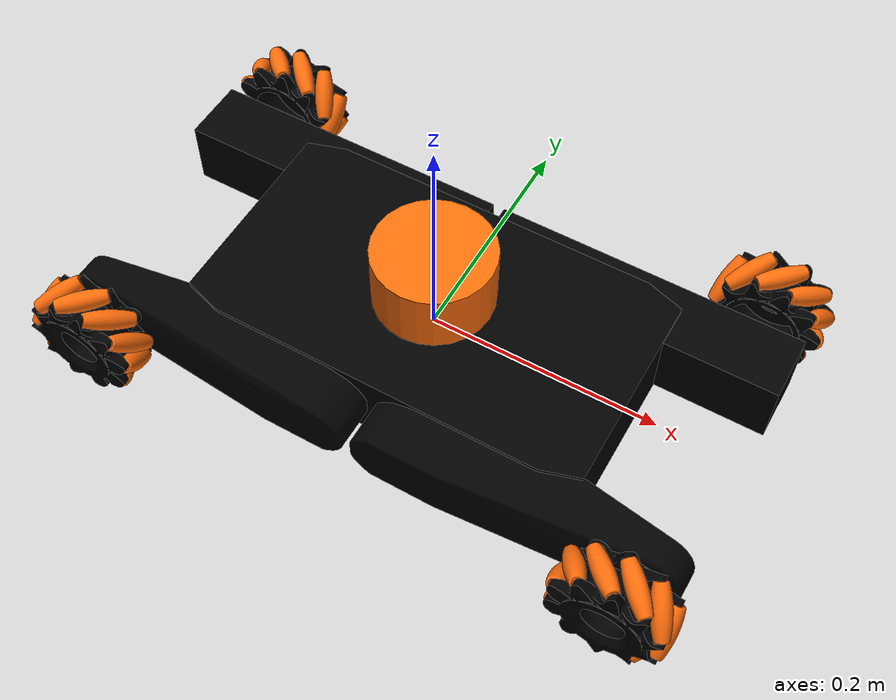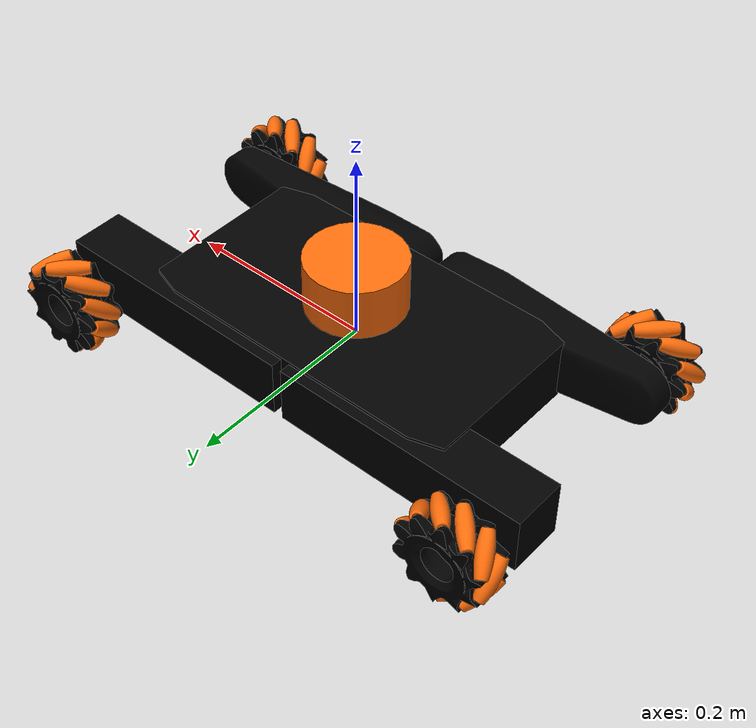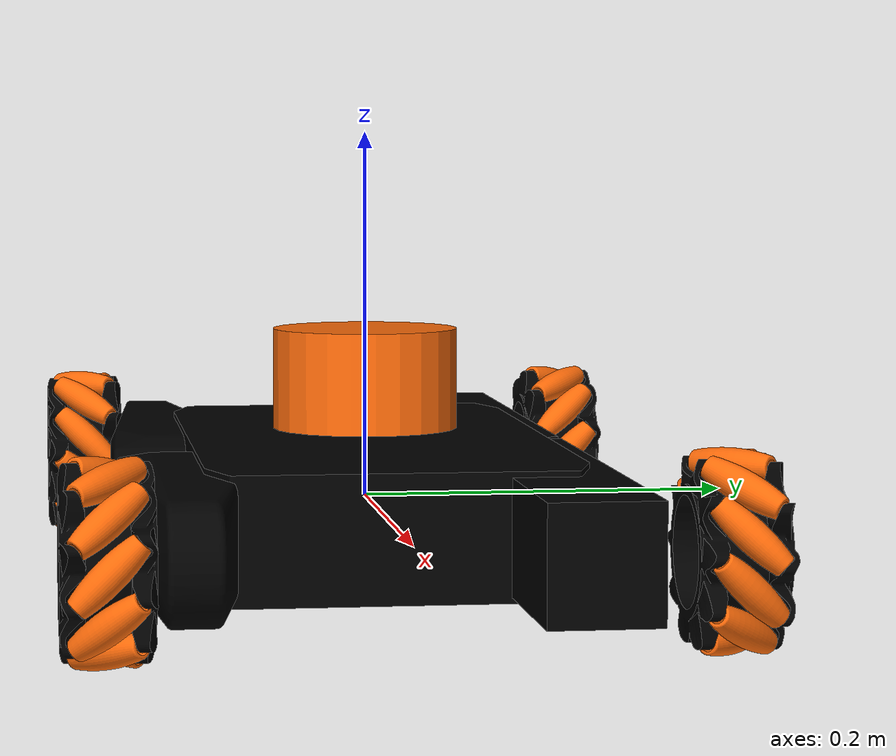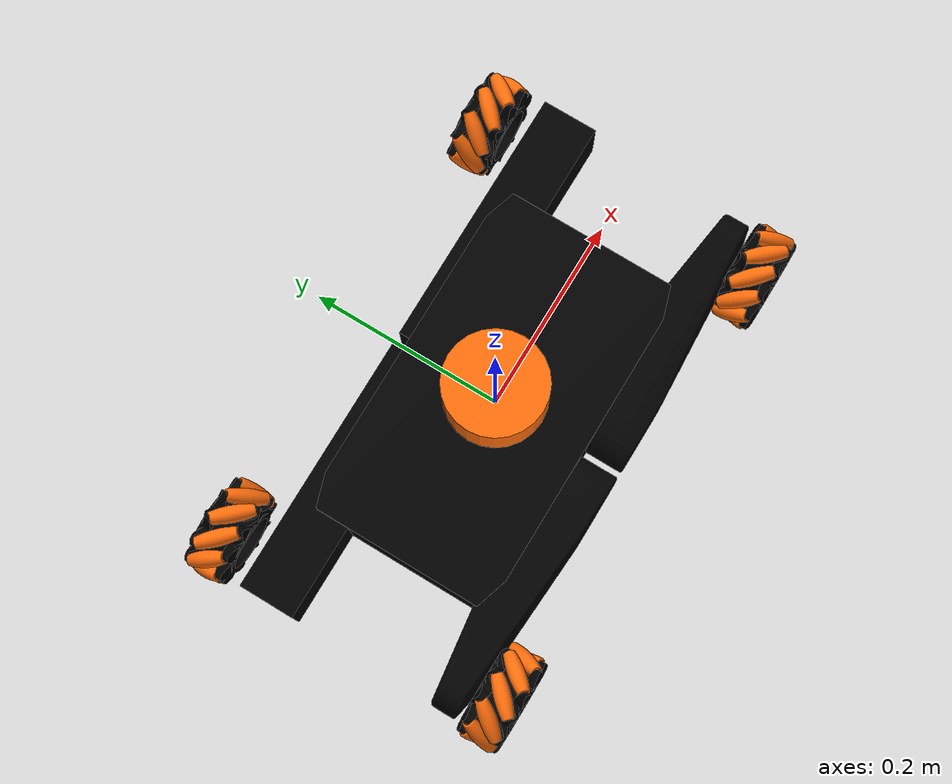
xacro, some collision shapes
<?xml version="1.0"?>
<robot name="mulinex" xmlns:xacro="http://ros.org/wiki/xacro">

    <xacro:include filename="$(find mulinex_description)/urdf/omni_car_module.xacro" />
    <xacro:property name="mulinex_base" value="file://$(find mulinex_description)/meshes//Body.stl" />
    <xacro:include filename="$(find mulinex_description)/urdf/material.xacro" />
    <xacro:include filename="$(find mulinex_description)/urdf/omnicar_ignition.xacro" />
    <xacro:include filename="$(find mulinex_description)/urdf/imu_sensor.xacro" />
    <xacro:include filename="$(find mulinex_description)/urdf/lidar_sensor.xacro" />
    <xacro:include filename="$(find mulinex_description)/urdf/camera_sensor.xacro" />

    <xacro:arg name="use_gazebo" default="true" />
    <xacro:arg name="yaml_file" default=""/>
    <xacro:arg name="lidar_3D" default="true"/>
    <xacro:arg name="omnicar_namespace" default="omnicar"/>

    <xacro:arg name="jnt_prefix" default=""/>

    <xacro:arg name="front_haa" default="0.0" />
    <xacro:arg name="hind_haa" default="0.0" />

    <link name="$(arg jnt_prefix)base_link">
        <visual>
            <material name="black"/>
            <origin xyz="0 0 0" rpy="0 0 0" />
            <geometry>
                <mesh filename="${mulinex_base}" />
            </geometry>
        </visual>
        <collision>
            <origin xyz="0 0 0" rpy="0 0 0" />
            <geometry>
                <box size="0.353 0.090 0.066" />
            </geometry>
        </collision>
        <inertial>
            <mass value="1.3008737" />
            <origin xyz="-1.4565496e-03 -2.5110071e-03 -4.2484136e-03" rpy="0 0 0" />
            <inertia ixx="4.0762590e-03" ixy="-2.5234809e-05" ixz="-3.2587794e-06"
                iyy="9.2413606e-03" iyz="-8.0660183e-06"
                izz="1.2268730e-02" />
        </inertial>

    </link>
    <gazebo>

        <plugin
            filename="ignition-gazebo-odometry-publisher-system"
            name="ignition::gazebo::systems::OdometryPublisher">
            <dimensions>3</dimensions>
            <odom_publish_frequency>100</odom_publish_frequency>
            <odom_frame>$(arg omnicar_namespace)/gt_odom</odom_frame>
            <robot_base_frame>$(arg omnicar_namespace)/base_link</robot_base_frame>
            <odom_topic>$(arg omnicar_namespace)/gt_odom</odom_topic>
            <tf_topic>$(arg omnicar_namespace)/gt_pose_gazebo</tf_topic>
        </plugin>
    </gazebo>
    <xacro:omni_mod
        prefix="LH"
        gazebo="$(arg use_gazebo)"
        jnt_pref="$(arg jnt_prefix)"
        simplify_meshes="true"
        />
    <xacro:omni_mod
        prefix="LF"
        gazebo="$(arg use_gazebo)"
        jnt_pref="$(arg jnt_prefix)"
        simplify_meshes="true"
        />
    <xacro:omni_mod
        prefix="RF"
        gazebo="$(arg use_gazebo)"
        jnt_pref="$(arg jnt_prefix)"
        simplify_meshes="true"
        />
    <xacro:omni_mod
        prefix="RH"
        gazebo="$(arg use_gazebo)"
        jnt_pref="$(arg jnt_prefix)"
        simplify_meshes="true"
    />
    <xacro:imu_sensor namespace="$(arg omnicar_namespace)"/>
    <xacro:lidar_sensor tredi="$(arg lidar_3D)" namespace="$(arg omnicar_namespace)"/>

    <xacro:omnicar_ign_hw
        gazebo="$(arg use_gazebo)"
        yaml="$(arg yaml_file)"
    />

</robot>

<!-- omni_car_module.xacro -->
<robot xmlns:xacro="http://ros.org/wiki/xacro">

    <xacro:include filename="$(find mulinex_description)/urdf/hip_module.xacro" />
    <xacro:include filename="$(find mulinex_description)/urdf/wheel.xacro" />
    <xacro:property name="PI" value="3.141592" />

    <xacro:macro name="omni_mod" params="prefix gazebo jnt_pref simplify_meshes">
        <!-- Module 1 -->
        <xacro:hip
            prefix="${prefix}"
            gazebo="${gazebo}"
            jnt_pref=""
            simplify_meshes="${simplify_meshes}"
        />
        <!-- wheel -->
        <xacro:wheel
            prefix="${prefix}"
            gazebo="${gazebo}"
        />

    </xacro:macro>

</robot>

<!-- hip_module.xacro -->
<robot xmlns:xacro="http://ros.org/wiki/xacro">

    <xacro:property name="base_2_HAA_y" value="${81.0 * 0.001}" />
    <xacro:property name="base_2_HAA_x" value="${45.0 * 0.001}" />
    <xacro:property name="PI" value="3.141592" />

    <!-- MULINEX VISUALIZATION meshes -->

    <xacro:property name="mulinex_module_left_front"
        value="file://$(find mulinex_description)/meshes//Module_left_front.stl" />
    <xacro:property name="mulinex_module_left_hind"
        value="file://$(find mulinex_description)/meshes//Module_left_hind.stl" />
    <xacro:property name="mulinex_module_2_left"
        value="file://$(find mulinex_description)/meshes//Module_2_left.stl" />
    <xacro:property name="mulinex_lower_leg_left"
        value="file://$(find mulinex_description)/meshes//Lower_leg_left.stl" />
    <xacro:property name="mulinex_module_right_front"
        value="file://$(find mulinex_description)/meshes//Module_right_front.stl" />
    <xacro:property name="mulinex_module_right_hind"
        value="file://$(find mulinex_description)/meshes//Module_right_hind.stl" />
    <xacro:property name="mulinex_module_2_right"
        value="file://$(find mulinex_description)/meshes//Module_2_right.stl" />
    <xacro:property name="mulinex_lower_leg_right"
        value="file://$(find mulinex_description)/meshes//Lower_leg_right.stl" />

    <!-- HIP -->
    <xacro:macro name="hip" params="prefix gazebo jnt_pref simplify_meshes">
        <!-- Transformation based on the position of each link -->
        <xacro:if value="${prefix == 'LF'}">
            <xacro:property name="base_to_hip_xyz" value="${base_2_HAA_x} ${base_2_HAA_y} 0" />
        </xacro:if>
        <xacro:if
            value="${prefix == 'LH'}">
            <xacro:property name="base_to_hip_xyz" value="${-base_2_HAA_x} ${base_2_HAA_y} 0" />
        </xacro:if>
        <xacro:if
            value="${prefix == 'RF'}">
            <xacro:property name="base_to_hip_xyz" value="${base_2_HAA_x} ${-base_2_HAA_y} 0" />
        </xacro:if>
        <xacro:if
            value="${prefix == 'RH'}">
            <xacro:property name="base_to_hip_xyz" value="${-base_2_HAA_x} ${-base_2_HAA_y} 0" />
        </xacro:if>

        <!-- Joint to fix the leg to the base -->
        <joint name="${prefix}_HAA" type="fixed">
            <parent link="${jnt_pref}base_link" />
            <child link="${jnt_pref}${prefix}_SHOULDER" />
            <origin xyz="${base_to_hip_xyz}" rpy="0 0 0" />
        </joint>
        <!-- Shoulder link -->
        <link name="${prefix}_SHOULDER">
            <visual>
                <material name="black" />
                <xacro:if value="${prefix == 'LF'}">
                    <origin xyz="0 0 0" rpy="0 0 0" />
                    <geometry>
                        <xacro:if value="${simplify_meshes}">
                            <mesh filename="${mulinex_module_left_front}" />
                        </xacro:if>
                        <xacro:unless value="${simplify_meshes}">
                            <mesh filename="${old_mulinex_module_left_front}" />
                        </xacro:unless>
                    </geometry>
                </xacro:if>
                <xacro:if value="${prefix == 'LH'}">
                    <origin xyz="0 0 0" rpy="0 0 0" />
                    <geometry>
                        <xacro:if value="${simplify_meshes}">
                            <mesh filename="${mulinex_module_left_hind}" />
                        </xacro:if>
                        <xacro:unless value="${simplify_meshes}">
                            <mesh filename="${old_mulinex_module_left_hind}" />
                        </xacro:unless>
                    </geometry>
                </xacro:if>
                <xacro:if value="${prefix == 'RF'}">
                    <origin xyz="0 0 0" rpy="0 0 0" />
                    <geometry>
                        <xacro:if value="${simplify_meshes}">
                            <mesh filename="${mulinex_module_right_front}" />
                        </xacro:if>
                        <xacro:unless value="${simplify_meshes}">
                            <mesh filename="${old_mulinex_module_right_front}" />
                        </xacro:unless>
                    </geometry>
                </xacro:if>
                <xacro:if value="${prefix == 'RH'}">
                    <origin xyz="0 0 0" rpy="0 0 0" />
                    <geometry>
                        <xacro:if value="${simplify_meshes}">
                            <mesh filename="${mulinex_module_right_hind}" />
                        </xacro:if>
                        <xacro:unless value="${simplify_meshes}">
                            <mesh filename="${old_mulinex_module_right_hind}" />
                        </xacro:unless>
                    </geometry>
                </xacro:if>
            </visual>

            <collision>
                <xacro:if value="${prefix == 'LF'}">
                    <origin xyz="0.0945 0 0" rpy="0 0 0" />
                    <geometry>
                        <box size="0.269 0.057 0.060" />
                    </geometry>
                </xacro:if>
                <xacro:if value="${prefix == 'LH'}">
                    <origin xyz="-0.0945 0 0" rpy="0 0 0" />
                    <geometry>
                        <box size="0.269 0.057 0.060" />
                    </geometry>
                </xacro:if>
                <xacro:if value="${prefix == 'RF'}">
                    <origin xyz="0.0945 0 0" rpy="0 0 0" />
                    <geometry>
                        <box size="0.269 0.057 0.060" />
                    </geometry>
                </xacro:if>
                <xacro:if value="${prefix == 'RH'}">
                    <origin xyz="-0.0945 0 0" rpy="0 0 0" />
                    <geometry>
                        <box size="0.269 0.057 0.060" />
                    </geometry>
                </xacro:if>
            </collision>

            <inertial>
                <mass value="0.47669673" />
                <xacro:if value="${prefix == 'LF'}">
                    <origin
                        xyz="7.2487360e-02 3.1582591e-02 -2.4812434e-03"
                        rpy="0 0 0" />
                    <inertia ixx="2.1574269e-04" ixy="-3.3437484e-05"
                        ixz="-2.4284668e-06" iyy="3.0607390e-03"
                        iyz="-2.0388977e-06" izz="3.0504273e-03" />
                </xacro:if>
                <xacro:if value="${prefix == 'LH'}">
                    <origin
                        xyz="-7.2487360e-02 3.1582591e-02 2.4812434e-03"
                        rpy="0 0 0" />
                    <inertia ixx="2.1574269e-04" ixy="3.3437484e-05"
                        ixz="-2.4284668e-06" iyy="3.0607390e-03"
                        iyz="-2.0388977e-06" izz="3.0504273e-03" />
                </xacro:if>
                <xacro:if value="${prefix == 'RF'}">
                    <origin
                        xyz="7.2487360e-02 -3.1582591e-02 2.4812434e-03"
                        rpy="0 0 0" />
                    <inertia ixx="2.1574269e-04" ixy="3.3437484e-05"
                        ixz="2.4284668e-06" iyy="3.0607390e-03"
                        iyz="-2.0388977e-06" izz="3.0504273e-03" />
                </xacro:if>
                <xacro:if value="${prefix == 'RH'}">
                    <origin
                        xyz="-7.2487360e-02 -3.1582591e-02 -2.4812434e-03"
                        rpy="0 0 0" />
                    <inertia ixx="2.1574269e-04" ixy="-3.3437484e-05"
                        ixz="2.4284668e-06" iyy="3.0607390e-03"
                        iyz="-2.0388977e-06" izz="3.0504273e-03" />
                </xacro:if>
            </inertial>
        </link>
        <xacro:if value="${gazebo}">
            <gazebo reference="${prefix}_SHOULDER">
                <collision>
                    <surface>
                        <friction>
                            <ode>
                                <mu>1</mu>
                                <mu2>1</mu2>
                                <slip1>0</slip1>
                                <slip2>0</slip2>
                            </ode>
                        </friction>
                        <contact>
                            <ode>
                                <kp>1000000.0</kp>
                                <kd>100.0</kd>
                                <min_depth>0.001</min_depth>
                            </ode>
                        </contact>
                    </surface>
                </collision>
            </gazebo>
        </xacro:if>
    </xacro:macro>

</robot>

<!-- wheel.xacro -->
<robot xmlns:xacro="http://ros.org/wiki/xacro">

    <xacro:property name="PI" value="3.141592" />

    <!-- Transformation based on the position of each link -->
     <!-- WHEEL Hip -->

    <xacro:property name="mulinex_roller"
        value="file://$(find mulinex_description)/meshes//roller_1.STL" />
    <xacro:property name="mulinex_mec_wheel_LF"
        value="file://$(find mulinex_description)/meshes//mecanum_wheel_lf.STL" />
    <xacro:property name="mulinex_mec_wheel_RF"
        value="file://$(find mulinex_description)/meshes//mecanum_wheel_rf.STL" />
    <xacro:property name="mulinex_mec_wheel_LH"
        value="file://$(find mulinex_description)/meshes//mecanum_wheel_lh.STL" />
    <xacro:property name="mulinex_mec_wheel_RH"
        value="file://$(find mulinex_description)/meshes//mecanum_wheel_rh.STL" />
    <xacro:property name="HAA_2_HFE_x" value="${190.0 * 0.001}" />
    <xacro:property name="HAA_2_HFE_y" value="${25.0 * 0.001}" />

        <!-- Transformation based on the position of each link -->

    <xacro:macro name="wheel" params="prefix gazebo">
        <joint name="${prefix}_WHEEL_JNT" type="continuous">
            <parent link="${prefix}_SHOULDER" />
            <child link="${prefix}_WHEEL" />
            <xacro:if value="${prefix == 'LF'}">
                <origin xyz="${HAA_2_HFE_x} ${HAA_2_HFE_y} 0" rpy="0 0 0" />
                <axis xyz="0 1 0" />
            </xacro:if>
            <xacro:if value="${prefix == 'LH'}">
                <origin xyz="${-HAA_2_HFE_x} ${HAA_2_HFE_y} 0" rpy="0 0 0" />
                <axis xyz="0 1 0" />
            </xacro:if>
            <xacro:if value="${prefix == 'RF'}">
                <origin xyz="${HAA_2_HFE_x} ${-HAA_2_HFE_y} 0" rpy="0 0 0" />
                <axis xyz="0 -1 0" />
            </xacro:if>
            <xacro:if value="${prefix == 'RH'}">
                <origin xyz="${-HAA_2_HFE_x} ${-HAA_2_HFE_y} 0" rpy="0 0 0" />
                <axis xyz="0 -1 0" />
            </xacro:if>
        </joint>
        <link name="${prefix}_WHEEL">

            <visual>
                <material name="black" />
                <xacro:if value="${prefix == 'LF'}">
                    <origin xyz="0 0 0" rpy="0 0 0" />
                    <geometry>
                        <mesh filename="${mulinex_mec_wheel_LF}" />
                    </geometry>
                </xacro:if>
                <xacro:if value="${prefix == 'LH'}">
                    <origin xyz="0 0  0" rpy="0 0 0" />
                    <geometry>
                        <mesh filename="${mulinex_mec_wheel_LH}" />
                    </geometry>
                </xacro:if>
                <xacro:if value="${prefix == 'RF'}">
                    <origin xyz="0 0 0" rpy="0 0 0" />
                    <geometry>
                        <mesh filename="${mulinex_mec_wheel_RF}" />
                    </geometry>
                </xacro:if>
                <xacro:if value="${prefix == 'RH'}">
                    <origin xyz="0 0 0" rpy="0 0 0" />
                    <geometry>
                        <mesh filename="${mulinex_mec_wheel_RH}" />
                    </geometry>
                </xacro:if>
            </visual>
            <!-- NO COLLISION FOR THE MECHANUM WHEELS -->
            <inertial>
                <xacro:if value="${prefix == 'LF'}">
                    <origin xyz="0 0.047255 -2.335E-07" rpy="0 0 0" />
                    <mass value="0.078919" />
                    <inertia ixx="4.9627E-05" ixy="1.7873E-11"
                        ixz="-2.2576E-09" iyy="7.8948E-05"
                        iyz="-7.6317E-12" izz="4.9622E-05" />
                </xacro:if>
                <xacro:if value="${prefix == 'LH'}">
                    <origin xyz="0 0.047255 -1.5525E-07" rpy="0 0 0" />
                    <mass value="0.078525" />
                    <inertia ixx="4.9627E-05" ixy="-2.1009E-12"
                        ixz="-1.8882E-09" iyy="7.8948E-05"
                        iyz="4.4431E-12" izz="4.9622E-05" />
                </xacro:if>
                <xacro:if value="${prefix == 'RF'}">
                    <origin xyz="0 -0.047255 -1.5525E-07" rpy="0 0 0" />
                    <mass value="0.078525" />
                    <inertia ixx="4.9627E-05" ixy="-2.1009E-12"
                        ixz="1.8882E-09" iyy="7.8948E-05"
                        iyz="-4.4431E-12" izz="4.9622E-05" />
                </xacro:if>
                <xacro:if value="${prefix == 'RH'}">
                    <origin xyz="0 -0.047255 -2.3351E-07" rpy="0 0 0" />
                    <mass value="0.078919" />
                    <inertia ixx="4.9627E-05" ixy="1.7873E-11"
                        ixz="-2.2576E-09" iyy="7.8948E-05"
                        iyz="-7.6317E-12" izz="4.9622E-05" />
                </xacro:if>
            </inertial>
        </link>
        <xacro:if value="${gazebo}">
            <gazebo reference="${prefix}_WHEEL">
                <collision>
                    <surface>
                        <friction>
                            <ode>
                                <mu>0.6</mu>
                                <mu2>0.6</mu2>
                                <slip1>0</slip1>
                                <slip2>0</slip2>
                            </ode>
                        </friction>
                        <contact>
                            <ode>
                                <kp>1000.0</kp>
                                <kd>10.0</kd>
                                <min_depth>0.001</min_depth>
                            </ode>
                        </contact>
                    </surface>
                </collision>
            </gazebo>
        </xacro:if>

        <link name="${prefix}_Roller1">
            <xacro:if value="${prefix == 'LF'}">
                <inertial>
                    <origin
                        xyz="0 0 6.3075E-15"
                        rpy="0 0 0" />
                    <mass
                        value="0.0059616" />
                    <inertia
                        ixx="7.911E-07"
                        ixy="1.2914E-12"
                        ixz="1.2242E-22"
                        iyy="7.9113E-07"
                        iyz="-5.294E-23"
                        izz="2.3532E-07" />
                </inertial>
                <visual>
                    <origin
                        xyz="0 0 0"
                        rpy="0 0 0" />
                    <geometry>
                        <mesh filename="${mulinex_roller}" />
                    </geometry>
                    <material name="orange"/>
                </visual>
                <collision>
                    <origin
                        xyz="0 0 0"
                        rpy="0 0 0" />
                    <geometry>
                        <mesh filename="${mulinex_roller}" />
                    </geometry>
                </collision>
            </xacro:if>
            <xacro:if value="${prefix == 'RF'}">
                <inertial>
                    <origin
                        xyz="0 0 0"
                        rpy="0 0 0" />
                    <mass
                        value="0.0059616" />
                    <inertia
                        ixx="7.911E-07"
                        ixy="1.2914E-12"
                        ixz="2.5808E-22"
                        iyy="7.9113E-07"
                        iyz="-5.4263E-22"
                        izz="2.3532E-07" />
                </inertial>
                <visual>
                    <origin
                        xyz="0 0 0"
                        rpy="0 0 0" />
                    <geometry>
                        <mesh filename="${mulinex_roller}" />
                    </geometry>
                    <material name="orange"/>
                </visual>
                <collision>
                    <origin
                        xyz="0 0 0"
                        rpy="0 0 0" />
                    <geometry>
                        <mesh filename="${mulinex_roller}" />
                    </geometry>
                </collision>
            </xacro:if>
            <xacro:if value="${prefix == 'LH'}">
                <inertial>
                    <origin
                        xyz="0 0 6.3075E-15"
                        rpy="0 0 0" />
                    <mass
                        value="0.0059616" />
                    <inertia
                        ixx="7.911E-07"
                        ixy="1.2914E-12"
                        ixz="1.9521E-22"
                        iyy="7.9113E-07"
                        iyz="-5.0954E-22"
                        izz="2.3532E-07" />
                </inertial>
                <visual>

                    <origin
                        xyz="0 0 0"
                        rpy="0 0 0" />
                    <geometry>
                        <mesh filename="${mulinex_roller}" />
                    </geometry>
                    <material name="orange"/>
                </visual>
                <collision>
                    <origin
                        xyz="0 0 0"
                        rpy="0 0 0" />
                    <geometry>
                        <mesh filename="${mulinex_roller}" />
                    </geometry>
                </collision>
            </xacro:if>
            <xacro:if value="${prefix == 'RH'}">
                <inertial>
                    <origin
                        xyz="0 0 6.3075E-15"
                        rpy="0 0 0" />
                    <mass
                        value="0.0059616" />
                    <inertia
                        ixx="7.911E-07"
                        ixy="1.2914E-12"
                        ixz="1.2242E-22"
                        iyy="7.9113E-07"
                        iyz="-5.294E-23"
                        izz="2.3532E-07" />
                </inertial>
                <visual>
                    <origin
                        xyz="0 0 0"
                        rpy="0 0 0" />
                    <geometry>
                        <mesh filename="${mulinex_roller}" />
                    </geometry>
                    <material name="orange"/>
                </visual>
                <collision>
                    <origin
                        xyz="0 0 0"
                        rpy="0 0 0" />
                    <geometry>
                        <mesh filename="${mulinex_roller}" />
                    </geometry>
                </collision>
            </xacro:if>
        </link>
        <xacro:if value="${gazebo}">
            <gazebo reference="${prefix}_Roller1">

                <collision>
                    <surface>
                        <friction>
                            <ode>
                                <mu>0.6</mu>
                                <mu2>0.6</mu2>
                                <slip1>0</slip1>
                                <slip2>0</slip2>
                            </ode>
                        </friction>
                        <contact>
                            <ode>
                                <kp>1000.0</kp>
                                <kd>10.0</kd>
                                <min_depth>0.001</min_depth>
                            </ode>
                        </contact>
                    </surface>
                </collision>

            </gazebo>
        </xacro:if>

        <link name="${prefix}_Roller2">
            <xacro:if value="${prefix == 'LF'}">
                <inertial>
                    <origin
                        xyz="0 0 6.3075E-15"
                        rpy="0 0 0" />
                    <mass
                        value="0.0059616" />
                    <inertia
                        ixx="7.911E-07"
                        ixy="1.2914E-12"
                        ixz="-2.0183E-22"
                        iyy="7.9113E-07"
                        iyz="2.8455E-22"
                        izz="2.3532E-07" />
                </inertial>
                <visual>
                    <origin
                        xyz="0 0 0"
                        rpy="0 0 0" />
                    <geometry>
                        <mesh filename="${mulinex_roller}" />
                    </geometry>
                    <material name="orange"/>
                </visual>
                <collision>
                    <origin
                        xyz="0 0 0"
                        rpy="0 0 0" />
                    <geometry>
                        <mesh filename="${mulinex_roller}" />
                    </geometry>
                </collision>
            </xacro:if>
            <xacro:if value="${prefix == 'RF'}">
                <inertial>
                    <origin
                        xyz="0 0 0"
                        rpy="0 0 0" />
                    <mass
                        value="0.0059616" />
                    <inertia
                        ixx="7.911E-07"
                        ixy="1.2914E-12"
                        ixz="1.4228E-22"
                        iyy="7.9113E-07"
                        iyz="-1.3301E-21"
                        izz="2.3532E-07" />
                </inertial>
                <visual>
                    <origin
                        xyz="0 0 0"
                        rpy="0 0 0" />
                    <geometry>
                        <mesh filename="${mulinex_roller}" />
                    </geometry>
                    <material name="orange"/>
                </visual>
                <collision>
                    <origin
                        xyz="0 0 0"
                        rpy="0 0 0" />
                    <geometry>
                        <mesh filename="${mulinex_roller}" />
                    </geometry>
                </collision>
            </xacro:if>
            <xacro:if value="${prefix == 'LH'}">
                <inertial>
                    <origin
                        xyz="0 0 6.3075E-15"
                        rpy="0 0 0" />
                    <mass
                        value="0.0059616" />
                    <inertia
                        ixx="7.911E-07"
                        ixy="1.2914E-12"
                        ixz="-7.6101E-23"
                        iyy="7.9113E-07"
                        iyz="1.522E-22"
                        izz="2.3532E-07" />
                </inertial>
                <visual>
                    <origin
                        xyz="0 0 0"
                        rpy="0 0 0" />
                    <geometry>
                        <mesh filename="${mulinex_roller}" />
                    </geometry>
                    <material name="orange"/>
                </visual>
                <collision>
                    <origin
                        xyz="0 0 0"
                        rpy="0 0 0" />
                    <geometry>
                        <mesh filename="${mulinex_roller}" />
                    </geometry>
                </collision>
            </xacro:if>
            <xacro:if value="${prefix == 'RH'}">
                <inertial>
                    <origin
                        xyz="0 0 6.3075E-15"
                        rpy="0 0 0" />
                    <mass
                        value="0.0059616" />
                    <inertia
                        ixx="7.911E-07"
                        ixy="1.2914E-12"
                        ixz="-1.7536E-22"
                        iyy="7.9113E-07"
                        iyz="2.2499E-22"
                        izz="2.3532E-07" />
                </inertial>
                <visual>
                    <origin
                        xyz="0 0 0"
                        rpy="0 0 0" />
                    <geometry>
                        <mesh filename="${mulinex_roller}" />
                    </geometry>
                    <material name="orange"/>
                </visual>
                <collision>
                    <origin
                        xyz="0 0 0"
                        rpy="0 0 0" />
                    <geometry>
                        <mesh filename="${mulinex_roller}" />
                    </geometry>
                </collision>
            </xacro:if>
        </link>
        <xacro:if value="${gazebo}">
            <gazebo reference="${prefix}_Rollert2">
                <collision>
                    <surface>
                        <friction>
                            <ode>
                                <mu>0.6</mu>
                                <mu2>0.6</mu2>
                                <slip1>0</slip1>
                                <slip2>0</slip2>
                            </ode>
                        </friction>
                        <contact>
                            <ode>
                                <kp>1000.0</kp>
                                <kd>10.0</kd>
                                <min_depth>0.001</min_depth>
                            </ode>
                        </contact>
                    </surface>
                </collision>
            </gazebo>
        </xacro:if>

        <link name="${prefix}_Roller3">
            <xacro:if value="${prefix == 'LF'}">
                <inertial>
                    <origin
                        xyz="0 0 6.3075E-15"
                        rpy="0 0 0" />
                    <mass
                        value="0.0059616" />
                    <inertia
                        ixx="7.911E-07"
                        ixy="1.2914E-12"
                        ixz="-2.9448E-22"
                        iyy="7.9113E-07"
                        iyz="-3.3749E-22"
                        izz="2.3532E-07" />
                </inertial>
                <visual>
                    <origin
                        xyz="0 0 0"
                        rpy="0 0 0" />
                    <geometry>
                        <mesh filename="${mulinex_roller}" />
                    </geometry>
                    <material name="orange"/>
                </visual>
                <collision>
                    <origin
                        xyz="0 0 0"
                        rpy="0 0 0" />
                    <geometry>
                        <mesh filename="${mulinex_roller}" />
                    </geometry>
                </collision>
            </xacro:if>
            <xacro:if value="${prefix == 'RF'}">
                <inertial>
                    <origin
                        xyz="0 0 6.3075E-15"
                        rpy="0 0 0" />
                    <mass
                        value="0.0059616" />
                    <inertia
                        ixx="7.911E-07"
                        ixy="1.2914E-12"
                        ixz="-7.6101E-23"
                        iyy="7.9113E-07"
                        iyz="2.1176E-22"
                        izz="2.3532E-07" />
                </inertial>
                <visual>
                    <origin
                        xyz="0 0 0"
                        rpy="0 0 0" />
                    <geometry>
                        <mesh filename="${mulinex_roller}" />
                    </geometry>
                    <material name="orange"/>
                </visual>
                <collision>
                    <origin
                        xyz="0 0 0"
                        rpy="0 0 0" />
                    <geometry>
                        <mesh filename="${mulinex_roller}" />
                    </geometry>
                </collision>
            </xacro:if>
            <xacro:if value="${prefix == 'LH'}">
                <inertial>
                    <origin
                        xyz="0 0 6.3075E-15"
                        rpy="0 0 0" />
                    <mass
                        value="0.0059616" />
                    <inertia
                        ixx="7.911E-07"
                        ixy="1.2914E-12"
                        ixz="-7.6101E-23"
                        iyy="7.9113E-07"
                        iyz="1.522E-22"
                        izz="2.3532E-07" />
                </inertial>
                <visual>
                    <origin
                        xyz="0 0 0"
                        rpy="0 0 0" />
                    <geometry>
                        <mesh filename="${mulinex_roller}" />
                    </geometry>
                    <material name="orange"/>
                </visual>
                <collision>
                    <origin
                        xyz="0 0 0"
                        rpy="0 0 0" />
                    <geometry>
                        <mesh filename="${mulinex_roller}" />
                    </geometry>
                </collision>
            </xacro:if>
            <xacro:if value="${prefix == 'RH'}">
                <inertial>
                    <origin
                        xyz="0 0 6.3075E-15"
                        rpy="0 0 0" />
                    <mass
                        value="0.0059616" />
                    <inertia
                        ixx="7.911E-07"
                        ixy="1.2914E-12"
                        ixz="-2.9448E-22"
                        iyy="7.9113E-07"
                        iyz="-3.3749E-22"
                        izz="2.3532E-07" />
                </inertial>
                <visual>
                    <origin
                        xyz="0 0 0"
                        rpy="0 0 0" />
                    <geometry>
                        <mesh filename="${mulinex_roller}" />
                    </geometry>
                    <material name="orange"/>
                </visual>
                <collision>
                    <origin
                        xyz="0 0 0"
                        rpy="0 0 0" />
                    <geometry>
                        <mesh filename="${mulinex_roller}" />
                    </geometry>
                </collision>
            </xacro:if>
        </link>
        <xacro:if value="${gazebo}">
            <gazebo reference="${prefix}_Roller3">
                                <collision>
                    <surface>
                        <friction>
                            <ode>
                                <mu>0.6</mu>
                                <mu2>0.6</mu2>
                                <slip1>0</slip1>
                                <slip2>0</slip2>
                            </ode>
                        </friction>
                        <contact>
                            <ode>
                                <kp>100.0</kp>
                                <kd>10.0</kd>
                                <min_depth>0.001</min_depth>
                            </ode>
                        </contact>
                    </surface>
                </collision>
            </gazebo>
        </xacro:if>

        <link name="${prefix}_Roller4">
            <xacro:if value="${prefix == 'LF'}">
                <inertial>
                    <origin
                        xyz="0 0 6.3075E-15"
                        rpy="0 0 0" />
                    <mass
                        value="0.0059616" />
                    <inertia
                        ixx="7.911E-07"
                        ixy="1.2914E-12"
                        ixz="1.0588E-22"
                        iyy="7.9113E-07"
                        iyz="3.7058E-22"
                        izz="2.3532E-07" />
                </inertial>
                <visual>
                    <origin
                        xyz="0 0 0"
                        rpy="0 0 0" />
                    <geometry>
                        <mesh filename="${mulinex_roller}" />
                    </geometry>
                    <material name="orange"/>
                </visual>
                <collision>
                    <origin
                        xyz="0 0 0"
                        rpy="0 0 0" />
                    <geometry>
                        <mesh filename="${mulinex_roller}" />
                    </geometry>
                </collision>
            </xacro:if>
            <xacro:if value="${prefix == 'RF'}">
                <inertial>
                    <origin
                        xyz="0 0 6.3075E-15"
                        rpy="0 0 0" />
                    <mass
                        value="0.0059616" />
                    <inertia
                        ixx="7.911E-07"
                        ixy="1.2914E-12"
                        ixz="2.4485E-22"
                        iyy="7.9113E-07"
                        iyz="5.0293E-22"
                        izz="2.3532E-07" />
                </inertial>
                <visual>
                    <origin
                        xyz="0 0 0"
                        rpy="0 0 0" />
                    <geometry>
                        <mesh filename="${mulinex_roller}" />
                    </geometry>
                    <material name="orange"/>
                </visual>
                <collision>
                    <origin
                        xyz="0 0 0"
                        rpy="0 0 0" />
                    <geometry>
                        <mesh filename="${mulinex_roller}" />
                    </geometry>
                </collision>
            </xacro:if>
            <xacro:if value="${prefix == 'LH'}">
                <inertial>
                    <origin
                        xyz="0 0 6.3075E-15"
                        rpy="0 0 0" />
                    <mass
                        value="0.0059616" />
                    <inertia
                        ixx="7.911E-07"
                        ixy="1.2914E-12"
                        ixz="2.4485E-22"
                        iyy="7.9113E-07"
                        iyz="5.0293E-22"
                        izz="2.3532E-07" />
                </inertial>
                <visual>
                    <origin
                        xyz="0 0 0"
                        rpy="0 0 0" />
                    <geometry>
                        <mesh filename="${mulinex_roller}" />
                    </geometry>
                    <material name="orange"/>
                </visual>
                <collision>
                    <origin
                        xyz="0 0 0"
                        rpy="0 0 0" />
                    <geometry>
                        <mesh filename="${mulinex_roller}" />
                    </geometry>
                </collision>
            </xacro:if>
            <xacro:if value="${prefix == 'RH'}">
                <inertial>
                    <origin
                        xyz="0 0 6.3075E-15"
                        rpy="0 0 0" />
                    <mass
                        value="0.0059616" />
                    <inertia
                        ixx="7.911E-07"
                        ixy="1.2914E-12"
                        ixz="1.0588E-22"
                        iyy="7.9113E-07"
                        iyz="3.7058E-22"
                        izz="2.3532E-07" />
                </inertial>
                <visual>
                    <origin
                        xyz="0 0 0"
                        rpy="0 0 0" />
                    <geometry>
                        <mesh filename="${mulinex_roller}" />
                    </geometry>
                    <material name="orange"/>
                </visual>
                <collision>
                    <origin
                        xyz="0 0 0"
                        rpy="0 0 0" />
                    <geometry>
                        <mesh filename="${mulinex_roller}" />
                    </geometry>
                </collision>
            </xacro:if>
        </link>
        <xacro:if value="${gazebo}">
            <gazebo reference="${prefix}_Roller4">
                <collision>
                    <surface>
                        <friction>
                            <ode>
                                <mu>0.6</mu>
                                <mu2>0.6</mu2>
                                <slip1>0</slip1>
                                <slip2>0</slip2>
                            </ode>
                        </friction>
                        <contact>
                            <ode>
                                <kp>1000.0</kp>
                                <kd>10.0</kd>
                                <min_depth>0.001</min_depth>
                            </ode>
                        </contact>
                    </surface>
                </collision>
            </gazebo>
        </xacro:if>

        <link name="${prefix}_Roller5">
            <xacro:if value="${prefix == 'LF'}">
                <inertial>
                    <origin
                        xyz="0 0 6.3075E-15"
                        rpy="0 0 0" />
                    <mass
                        value="0.0059616" />
                    <inertia
                        ixx="7.911E-07"
                        ixy="1.2914E-12"
                        ixz="-1.2242E-22"
                        iyy="7.9113E-07"
                        iyz="-1.3235E-22"
                        izz="2.3532E-07" />
                </inertial>
                <visual>
                    <origin
                        xyz="0 0 0"
                        rpy="0 0 0" />
                    <geometry>
                        <mesh filename="${mulinex_roller}" />
                    </geometry>
                    <material name="orange"/>
                </visual>
                <collision>
                    <origin
                        xyz="0 0 0"
                        rpy="0 0 0" />
                    <geometry>
                        <mesh filename="${mulinex_roller}" />
                    </geometry>
                </collision>
            </xacro:if>
            <xacro:if value="${prefix == 'RF'}">
                <inertial>
                    <origin
                        xyz="0 0 6.3075E-15"
                        rpy="0 0 0" />
                    <mass
                        value="0.0059616" />
                    <inertia
                        ixx="7.911E-07"
                        ixy="1.2914E-12"
                        ixz="-8.2718E-23"
                        iyy="7.9113E-07"
                        iyz="3.1764E-22"
                        izz="2.3532E-07" />
                </inertial>
                <visual>
                    <origin
                        xyz="0 0 0"
                        rpy="0 0 0" />
                    <geometry>
                        <mesh filename="${mulinex_roller}" />
                    </geometry>
                    <material name="orange"/>
                </visual>
                <collision>
                    <origin
                        xyz="0 0 0"
                        rpy="0 0 0" />
                    <geometry>
                        <mesh filename="${mulinex_roller}" />
                    </geometry>
                </collision>
            </xacro:if>
            <xacro:if value="${prefix == 'LH'}">
                <inertial>
                    <origin
                        xyz="0 0 6.3075E-15"
                        rpy="0 0 0" />
                    <mass
                        value="0.0059616" />
                    <inertia
                        ixx="7.911E-07"
                        ixy="1.2914E-12"
                        ixz="-8.2718E-23"
                        iyy="7.9113E-07"
                        iyz="3.1764E-22"
                        izz="2.3532E-07" />
                </inertial>
                <visual>
                    <origin
                        xyz="0 0 0"
                        rpy="0 0 0" />
                    <geometry>
                        <mesh filename="${mulinex_roller}" />
                    </geometry>
                    <material name="orange"/>
                </visual>
                <collision>
                    <origin
                        xyz="0 0 0"
                        rpy="0 0 0" />
                    <geometry>
                        <mesh filename="${mulinex_roller}" />
                    </geometry>
                </collision>
            </xacro:if>
            <xacro:if value="${prefix == 'RH'}">
                <inertial>
                    <origin
                        xyz="0 0 6.3075E-15"
                        rpy="0 0 0" />
                    <mass
                        value="0.0059616" />
                    <inertia
                        ixx="7.911E-07"
                        ixy="1.2914E-12"
                        ixz="-1.2242E-22"
                        iyy="7.9113E-07"
                        iyz="-1.3235E-22"
                        izz="2.3532E-07" />
                </inertial>
                <visual>
                    <origin
                        xyz="0 0 0"
                        rpy="0 0 0" />
                    <geometry>
                        <mesh filename="${mulinex_roller}" />
                    </geometry>
                    <material name="orange"/>
                </visual>
                <collision>
                    <origin
                        xyz="0 0 0"
                        rpy="0 0 0" />
                    <geometry>
                        <mesh filename="${mulinex_roller}" />
                    </geometry>
                </collision>
            </xacro:if>
        </link>
        <xacro:if value="${gazebo}">
            <gazebo reference="${prefix}_Roller5">
                <collision>
                    <surface>
                        <friction>
                            <ode>
                                <mu>0.6</mu>
                                <mu2>0.6</mu2>
                                <slip1>0</slip1>
                                <slip2>0</slip2>
                            </ode>
                        </friction>
                        <contact>
                            <ode>
                                <kp>1000.0</kp>
                                <kd>10.0</kd>
                                <min_depth>0.001</min_depth>
                            </ode>
                        </contact>
                    </surface>
                </collision>
            </gazebo>
        </xacro:if>

        <link name="${prefix}_Roller6">
            <xacro:if value="${prefix == 'LF'}">
                <inertial>
                    <origin
                        xyz="0 0 6.3075E-15"
                        rpy="0 0 0" />
                    <mass
                        value="0.0059616" />
                    <inertia
                        ixx="7.911E-07"
                        ixy="1.2914E-12"
                        ixz="1.1911E-22"
                        iyy="7.9113E-07"
                        iyz="1.2573E-22"
                        izz="2.3532E-07" />
                </inertial>
                <visual>
                    <origin
                        xyz="0 0 0"
                        rpy="0 0 0" />
                    <geometry>
                        <mesh filename="${mulinex_roller}" />
                    </geometry>
                    <material name="orange"/>
                </visual>
                <collision>
                    <origin
                        xyz="0 0 0"
                        rpy="0 0 0" />
                    <geometry>
                        <mesh filename="${mulinex_roller}" />
                    </geometry>
                </collision>
            </xacro:if>
            <xacro:if value="${prefix == 'RF'}">
                <inertial>
                    <origin
                        xyz="0 0 6.3075E-15"
                        rpy="0 0 0" />
                    <mass
                        value="0.0059616" />
                    <inertia
                        ixx="7.911E-07"
                        ixy="1.2914E-12"
                        ixz="3.6396E-23"
                        iyy="7.9113E-07"
                        iyz="0"
                        izz="2.3532E-07" />
                </inertial>
                <visual>
                    <origin
                        xyz="0 0 0"
                        rpy="0 0 0" />
                    <geometry>
                        <mesh filename="${mulinex_roller}" />
                    </geometry>
                    <material name="orange"/>
                </visual>
                <collision>
                    <origin
                        xyz="0 0 0"
                        rpy="0 0 0" />
                    <geometry>
                        <mesh filename="${mulinex_roller}" />
                    </geometry>
                </collision>
            </xacro:if>
            <xacro:if value="${prefix == 'LH'}">
                <inertial>
                    <origin
                        xyz="0 0 6.3075E-15"
                        rpy="0 0 0" />
                    <mass
                        value="0.0059616" />
                    <inertia
                        ixx="7.911E-07"
                        ixy="1.2914E-12"
                        ixz="1.3235E-23"
                        iyy="7.9113E-07"
                        iyz="1.3235E-23"
                        izz="2.3532E-07" />
                </inertial>
                <visual>
                    <origin
                        xyz="0 0 0"
                        rpy="0 0 0" />
                    <geometry>
                        <mesh filename="${mulinex_roller}" />
                    </geometry>
                    <material name="orange"/>
                </visual>
                <collision>
                    <origin
                        xyz="0 0 0"
                        rpy="0 0 0" />
                    <geometry>
                        <mesh filename="${mulinex_roller}" />
                    </geometry>
                </collision>
            </xacro:if>
            <xacro:if value="${prefix == 'RH'}">
                <inertial>
                    <origin
                        xyz="0 0 6.3075E-15"
                        rpy="0 0 0" />
                    <mass
                        value="0.0059616" />
                    <inertia
                        ixx="7.911E-07"
                        ixy="1.2914E-12"
                        ixz="1.1911E-22"
                        iyy="7.9113E-07"
                        iyz="1.2573E-22"
                        izz="2.3532E-07" />
                </inertial>
                <visual>
                    <origin
                        xyz="0 0 0"
                        rpy="0 0 0" />
                    <geometry>
                        <mesh filename="${mulinex_roller}" />
                    </geometry>
                    <material name="orange"/>
                </visual>
                <collision>
                    <origin
                        xyz="0 0 0"
                        rpy="0 0 0" />
                    <geometry>
                        <mesh filename="${mulinex_roller}" />
                    </geometry>
                </collision>
            </xacro:if>
        </link>
        <xacro:if value="${gazebo}">
            <gazebo reference="${prefix}_Roller6">
                <collision>
                    <surface>
                        <friction>
                            <ode>
                                <mu>0.6</mu>
                                <mu2>0.6</mu2>
                                <slip1>0</slip1>
                                <slip2>0</slip2>
                            </ode>
                        </friction>
                        <contact>
                            <ode>
                                <kp>1000.0</kp>
                                <kd>10.0</kd>
                                <min_depth>0.001</min_depth>
                            </ode>
                        </contact>
                    </surface>
                </collision>
            </gazebo>
        </xacro:if>

        <link name="${prefix}_Roller7">
            <xacro:if value="${prefix == 'LF'}">
                <inertial>
                    <origin
                        xyz="0 0 6.3075E-15"
                        rpy="0 0 0" />
                    <mass
                        value="0.0059616" />
                    <inertia
                        ixx="7.911E-07"
                        ixy="1.2914E-12"
                        ixz="5.9557E-23"
                        iyy="7.9113E-07"
                        iyz="7.9409E-23"
                        izz="2.3532E-07" />
                </inertial>
                <visual>
                    <origin
                        xyz="0 0 0"
                        rpy="0 0 0" />
                    <geometry>
                        <mesh filename="${mulinex_roller}" />
                    </geometry>
                    <material name="orange"/>
                </visual>
                <collision>
                    <origin
                        xyz="0 0 0"
                        rpy="0 0 0" />
                    <geometry>
                        <mesh filename="${mulinex_roller}" />
                    </geometry>
                </collision>
            </xacro:if>
            <xacro:if value="${prefix == 'RF'}">
                <inertial>
                    <origin
                        xyz="0 0 6.3075E-15"
                        rpy="0 0 0" />
                    <mass
                        value="0.0059616" />
                    <inertia
                        ixx="7.911E-07"
                        ixy="1.2914E-12"
                        ixz="2.283E-22"
                        iyy="7.9113E-07"
                        iyz="-8.2718E-22"
                        izz="2.3532E-07" />
                </inertial>
                <visual>
                    <origin
                        xyz="0 0 0"
                        rpy="0 0 0" />
                    <geometry>
                        <mesh filename="${mulinex_roller}" />
                    </geometry>
                    <material name="orange"/>
                </visual>
                <collision>
                    <origin
                        xyz="0 0 0"
                        rpy="0 0 0" />
                    <geometry>
                        <mesh filename="${mulinex_roller}" />
                    </geometry>
                </collision>
            </xacro:if>
            <xacro:if value="${prefix == 'LH'}">
                <inertial>
                    <origin
                        xyz="0 0 6.3075E-15"
                        rpy="0 0 0" />
                    <mass
                        value="0.0059616" />
                    <inertia
                        ixx="7.9113E-07"
                        ixy="-9.1022E-13"
                        ixz="-8.4703E-22"
                        iyy="7.911E-07"
                        iyz="-2.8124E-22"
                        izz="2.3532E-07" />
                </inertial>
                <visual>
                    <origin
                        xyz="0 0 0"
                        rpy="0 0 0" />
                    <geometry>
                        <mesh filename="${mulinex_roller}" />
                    </geometry>
                    <material name="orange"/>
                </visual>
                <collision>
                    <origin
                        xyz="0 0 0"
                        rpy="0 0 0" />
                    <geometry>
                        <mesh filename="${mulinex_roller}" />
                    </geometry>
                </collision>
            </xacro:if>
            <xacro:if value="${prefix == 'RH'}">
                <inertial>
                    <origin
                        xyz="0 0 6.3075E-15"
                        rpy="0 0 0" />
                    <mass
                        value="0.0059616" />
                    <inertia
                        ixx="7.911E-07"
                        ixy="1.2914E-12"
                        ixz="8.6027E-23"
                        iyy="7.9113E-07"
                        iyz="6.6174E-23"
                        izz="2.3532E-07" />
                </inertial>
                <visual>
                    <origin
                        xyz="0 0 0"
                        rpy="0 0 0" />
                    <geometry>
                        <mesh filename="${mulinex_roller}" />
                    </geometry>
                    <material name="orange"/>
                </visual>
                <collision>
                    <origin
                        xyz="0 0 0"
                        rpy="0 0 0" />
                    <geometry>
                        <mesh filename="${mulinex_roller}" />
                    </geometry>
                </collision>
            </xacro:if>
        </link>
        <xacro:if value="${gazebo}">
            <gazebo reference="${prefix}_Roller7">
                <collision>
                    <surface>
                        <friction>
                            <ode>
                                <mu>0.6</mu>
                                <mu2>0.6</mu2>
                                <slip1>0</slip1>
                                <slip2>0</slip2>
                            </ode>
                        </friction>
                        <contact>
                            <ode>
                                <kp>1000.0</kp>
                                <kd>10.0</kd>
                                <min_depth>0.001</min_depth>
                            </ode>
                        </contact>
                    </surface>
                </collision>
            </gazebo>
        </xacro:if>

        <link name="${prefix}_Roller8">
            <xacro:if value="${prefix == 'LF'}">
                <inertial>
                    <origin
                        xyz="0 0 6.3075E-15"
                        rpy="0 0 0" />
                    <mass
                        value="0.0059616" />
                    <inertia
                        ixx="7.911E-07"
                        ixy="1.2914E-12"
                        ixz="-1.8529E-22"
                        iyy="7.9113E-07"
                        iyz="-3.1764E-22"
                        izz="2.3532E-07" />
                </inertial>
                <visual>
                    <origin
                        xyz="0 0 0"
                        rpy="0 0 0" />
                    <geometry>
                        <mesh filename="${mulinex_roller}" />
                    </geometry>
                    <material name="orange"/>
                </visual>
                <collision>
                    <origin
                        xyz="0 0 0"
                        rpy="0 0 0" />
                    <geometry>
                        <mesh filename="${mulinex_roller}" />
                    </geometry>
                </collision>
            </xacro:if>
            <xacro:if value="${prefix == 'RF'}">
                <inertial>
                    <origin
                        xyz="0 0 6.3075E-15"
                        rpy="0 0 0" />
                    <mass
                        value="0.0059616" />
                    <inertia
                        ixx="7.911E-07"
                        ixy="1.2914E-12"
                        ixz="4.3013E-23"
                        iyy="7.9113E-07"
                        iyz="-5.294E-22"
                        izz="2.3532E-07" />
                </inertial>
                <visual>
                    <origin
                        xyz="0 0 0"
                        rpy="0 0 0" />
                    <geometry>
                        <mesh filename="${mulinex_roller}" />
                    </geometry>
                    <material name="orange"/>
                </visual>
                <collision>
                    <origin
                        xyz="0 0 0"
                        rpy="0 0 0" />
                    <geometry>
                        <mesh filename="${mulinex_roller}" />
                    </geometry>
                </collision>
            </xacro:if>
            <xacro:if value="${prefix == 'LH'}">
                <inertial>
                    <origin
                        xyz="0 0 6.3075E-15"
                        rpy="0 0 0" />
                    <mass
                        value="0.0059616" />
                    <inertia
                        ixx="7.911E-07"
                        ixy="1.2914E-12"
                        ixz="4.3013E-23"
                        iyy="7.9113E-07"
                        iyz="-5.294E-22"
                        izz="2.3532E-07" />
                </inertial>
                <visual>
                    <origin
                        xyz="0 0 0"
                        rpy="0 0 0" />
                    <geometry>
                        <mesh filename="${mulinex_roller}" />
                    </geometry>
                    <material name="orange"/>
                </visual>
                <collision>
                    <origin
                        xyz="0 0 0"
                        rpy="0 0 0" />
                    <geometry>
                        <mesh filename="${mulinex_roller}" />
                    </geometry>
                </collision>
            </xacro:if>
            <xacro:if value="${prefix == 'RH'}">
                <inertial>
                    <origin
                        xyz="0 0 6.3075E-15"
                        rpy="0 0 0" />
                    <mass
                        value="0.0059616" />
                    <inertia
                        ixx="7.911E-07"
                        ixy="1.2914E-12"
                        ixz="-1.9852E-22"
                        iyy="7.9113E-07"
                        iyz="-3.1764E-22"
                        izz="2.3532E-07" />
                </inertial>
                <visual>
                    <origin
                        xyz="0 0 0"
                        rpy="0 0 0" />
                    <geometry>
                        <mesh filename="${mulinex_roller}" />
                    </geometry>
                    <material name="orange"/>
                </visual>
                <collision>
                    <origin
                        xyz="0 0 0"
                        rpy="0 0 0" />
                    <geometry>
                        <mesh filename="${mulinex_roller}" />
                    </geometry>
                </collision>
            </xacro:if>
        </link>
        <xacro:if value="${gazebo}">
            <gazebo reference="${prefix}_Roller8">
                <collision>
                    <surface>
                        <friction>
                            <ode>
                                <mu>0.6</mu>
                                <mu2>0.6</mu2>
                                <slip1>0</slip1>
                                <slip2>0</slip2>
                            </ode>
                        </friction>
                        <contact>
                            <ode>
                                <kp>1000.0</kp>
                                <kd>10.0</kd>
                                <min_depth>0.001</min_depth>
                            </ode>
                        </contact>
                    </surface>
                </collision>
            </gazebo>
        </xacro:if>

        <link name="${prefix}_Roller9">
            <xacro:if value="${prefix == 'LF'}">
                <inertial>
                    <origin
                        xyz="0 0 6.3075E-15"
                        rpy="0 0 0" />
                    <mass
                        value="0.0059616" />
                    <inertia
                        ixx="7.911E-07"
                        ixy="1.2914E-12"
                        ixz="1.3897E-22"
                        iyy="7.9113E-07"
                        iyz="-6.6174E-24"
                        izz="2.3532E-07" />
                </inertial>
                <visual>
                    <origin
                        xyz="0 0 0"
                        rpy="0 0 0" />
                    <geometry>
                        <mesh filename="${mulinex_roller}" />
                    </geometry>
                    <material name="orange"/>
                </visual>
                <collision>
                    <origin
                        xyz="0 0 0"
                        rpy="0 0 0" />
                    <geometry>
                        <mesh filename="${mulinex_roller}" />
                    </geometry>
                </collision>
            </xacro:if>
            <xacro:if value="${prefix == 'RF'}">
                <inertial>
                    <origin
                        xyz="0 0 6.3075E-15"
                        rpy="0 0 0" />
                    <mass
                        value="0.0059616" />
                    <inertia
                        ixx="7.911E-07"
                        ixy="1.2914E-12"
                        ixz="1.7205E-22"
                        iyy="7.9113E-07"
                        iyz="7.2792E-23"
                        izz="2.3532E-07" />
                </inertial>
                <visual>
                    <origin
                        xyz="0 0 0"
                        rpy="0 0 0" />
                    <geometry>
                        <mesh filename="${mulinex_roller}" />
                    </geometry>
                    <material name="orange"/>
                </visual>
                <collision>
                    <origin
                        xyz="0 0 0"
                        rpy="0 0 0" />
                    <geometry>
                        <mesh filename="${mulinex_roller}" />
                    </geometry>
                </collision>
            </xacro:if>
            <xacro:if value="${prefix == 'LH'}">
                <inertial>
                    <origin
                        xyz="0 0 6.3075E-15"
                        rpy="0 0 0" />
                    <mass
                        value="0.0059616" />
                    <inertia
                        ixx="7.911E-07"
                        ixy="1.2914E-12"
                        ixz="1.7205E-22"
                        iyy="7.9113E-07"
                        iyz="7.2792E-23"
                        izz="2.3532E-07" />
                </inertial>
                <visual>
                    <origin
                        xyz="0 0 0"
                        rpy="0 0 0" />
                    <geometry>
                        <mesh filename="${mulinex_roller}" />
                    </geometry>
                    <material name="orange"/>
                </visual>
                <collision>
                    <origin
                        xyz="0 0 0"
                        rpy="0 0 0" />
                    <geometry>
                        <mesh filename="${mulinex_roller}" />
                    </geometry>
                </collision>
            </xacro:if>
            <xacro:if value="${prefix == 'RH'}">
                <inertial>
                    <origin
                        xyz="0 0 6.3075E-15"
                        rpy="0 0 0" />
                    <mass
                        value="0.0059616" />
                    <inertia
                        ixx="7.911E-07"
                        ixy="1.2914E-12"
                        ixz="1.3897E-22"
                        iyy="7.9113E-07"
                        iyz="-6.6174E-24"
                        izz="2.3532E-07" />
                </inertial>
                <visual>
                    <origin
                        xyz="0 0 0"
                        rpy="0 0 0" />
                    <geometry>
                        <mesh filename="${mulinex_roller}" />
                    </geometry>
                    <material name="orange"/>
                </visual>
                <collision>
                    <origin
                        xyz="0 0 0"
                        rpy="0 0 0" />
                    <geometry>
                        <mesh filename="${mulinex_roller}" />
                    </geometry>
                </collision>
            </xacro:if>
        </link>
        <xacro:if value="${gazebo}">
            <gazebo reference="${prefix}_Roller9">
                <collision>
                    <surface>
                        <friction>
                            <ode>
                                <mu>0.6</mu>
                                <mu2>0.6</mu2>
                                <slip1>0</slip1>
                                <slip2>0</slip2>
                            </ode>
                        </friction>
                        <contact>
                            <ode>
                                <kp>1000.0</kp>
                                <kd>10.0</kd>
                                <min_depth>0.001</min_depth>
                            </ode>
                        </contact>
                    </surface>
                </collision>
            </gazebo>
        </xacro:if>

        <link name="${prefix}_Roller10">
            <xacro:if value="${prefix == 'LF'}">
                <inertial>
                    <origin
                        xyz="0 0 6.3075E-15"
                        rpy="0 0 0" />
                    <mass
                        value="0.0059616" />
                    <inertia
                        ixx="7.911E-07"
                        ixy="1.2914E-12"
                        ixz="-1.6544E-22"
                        iyy="7.9113E-07"
                        iyz="-3.9705E-23"
                        izz="2.3532E-07" />
                </inertial>
                <visual>
                    <origin
                        xyz="0 0 0"
                        rpy="0 0 0" />
                    <geometry>
                        <mesh filename="${mulinex_roller}" />
                    </geometry>
                    <material name="orange"/>
                </visual>
                <collision>
                    <origin
                        xyz="0 0 0"
                        rpy="0 0 0" />
                    <geometry>
                        <mesh filename="${mulinex_roller}" />
                    </geometry>
                </collision>
            </xacro:if>
            <xacro:if value="${prefix == 'RF'}">
                <inertial>
                    <origin
                        xyz="0 0 6.3075E-15"
                        rpy="0 0 0" />
                    <mass
                        value="0.0059616" />
                    <inertia
                        ixx="7.911E-07"
                        ixy="1.2914E-12"
                        ixz="-7.2792E-23"
                        iyy="7.9113E-07"
                        iyz="5.294E-23"
                        izz="2.3532E-07" />
                </inertial>
                <visual>
                    <origin
                        xyz="0 0 0"
                        rpy="0 0 0" />
                    <geometry>
                        <mesh filename="${mulinex_roller}" />
                    </geometry>
                    <material name="orange"/>
                </visual>
                <collision>
                    <origin
                        xyz="0 0 0"
                        rpy="0 0 0" />
                    <geometry>
                        <mesh filename="${mulinex_roller}" />
                    </geometry>
                </collision>
            </xacro:if>
            <xacro:if value="${prefix == 'LH'}">
                <inertial>
                    <origin
                        xyz="0 0 6.3075E-15"
                        rpy="0 0 0" />
                    <mass
                        value="0.0059616" />
                    <inertia
                        ixx="7.911E-07"
                        ixy="1.2914E-12"
                        ixz="-7.2792E-23"
                        iyy="7.9113E-07"
                        iyz="5.294E-23"
                        izz="2.3532E-07" />
                </inertial>
                <visual>
                    <origin
                        xyz="0 0 0"
                        rpy="0 0 0" />
                    <geometry>
                        <mesh filename="${mulinex_roller}" />
                    </geometry>
                    <material name="orange"/>
                </visual>
                <collision>
                    <origin
                        xyz="0 0 0"
                        rpy="0 0 0" />
                    <geometry>
                        <mesh filename="${mulinex_roller}" />
                    </geometry>
                </collision>
            </xacro:if>
            <xacro:if value="${prefix == 'RH'}">
                <inertial>
                    <origin
                        xyz="0 0 6.3075E-15"
                        rpy="0 0 0" />
                    <mass
                        value="0.0059616" />
                    <inertia
                        ixx="7.911E-07"
                        ixy="1.2914E-12"
                        ixz="-1.8529E-22"
                        iyy="7.9113E-07"
                        iyz="-6.6174E-24"
                        izz="2.3532E-07" />
                </inertial>
                <visual>
                    <origin
                        xyz="0 0 0"
                        rpy="0 0 0" />
                    <geometry>
                        <mesh filename="${mulinex_roller}" />
                    </geometry>
                    <material name="orange"/>
                </visual>
                <collision>
                    <origin
                        xyz="0 0 0"
                        rpy="0 0 0" />
                    <geometry>
                        <mesh filename="${mulinex_roller}" />
                    </geometry>
                </collision>
            </xacro:if>
        </link>
        <xacro:if value="${gazebo}">
            <gazebo reference="${prefix}_Roller10">
                <collision>
                    <surface>
                        <friction>
                            <ode>
                                <mu>0.6</mu>
                                <mu2>0.6</mu2>
                                <slip1>0</slip1>
                                <slip2>0</slip2>
                            </ode>
                        </friction>
                        <contact>
                            <ode>
                                <kp>1000.0</kp>
                                <kd>10.0</kd>
                                <min_depth>0.001</min_depth>
                            </ode>
                        </contact>
                    </surface>
                </collision>
            </gazebo>
        </xacro:if>

            <joint name="${prefix}_rol1" type="continuous">
                <parent link="${prefix}_WHEEL" />
                <child link="${prefix}_Roller1" />
                <xacro:if value="${prefix == 'LF'}">
                    <axis xyz="0 0 -1" />
                    <origin xyz="-0.039707 0.04345 -0.012901" rpy="-2.5315 0.60848 2.7559" />
                </xacro:if>
                <xacro:if value="${prefix == 'LH'}">
                    <axis xyz="0 0 -1" />
                    <origin xyz="0.033776 0.04345 0.02454" rpy="-0.46325 -0.87701 -0.46325" />
                </xacro:if>
                <xacro:if value="${prefix == 'RF'}">
                    <axis xyz="0 0 -1" />
                    <origin
                        xyz="-0.033776 -0.04345 0.024540037909306"
                        rpy="-0.463248165454369 -0.877005281485064 2.67834448813542" />
                </xacro:if>
                <xacro:if value="${prefix == 'RH'}">
                    <axis xyz="0 0 -1" />
                    <origin xyz="0.039707 -0.04345 -0.012901" rpy="-2.5315 0.60848 -0.38574" />
                </xacro:if>
            </joint>

            <joint name="${prefix}_rol2" type="continuous">
                <parent link="${prefix}_WHEEL" />
                <child link="${prefix}_Roller2" />
                <xacro:if value="${prefix == 'LF'}">
                    <axis xyz="0 0 -1" />
                    <origin xyz="-0.02454 0.04345 -0.033776" rpy="-3.0918 1.1416 2.3058" />
                </xacro:if>
                <xacro:if value="${prefix == 'LH'}">
                    <axis xyz="0 0 -1 " />
                    <origin xyz="0.0129 0.04345 0.039707" rpy="0.70109 -1.2808 -1.5327" />
                </xacro:if>
                <xacro:if value="${prefix == 'RF'}">
                    <axis xyz="0 0 -1 " />
                    <origin
                        xyz="-0.0129 -0.04345 0.0397066131814208"
                        rpy="0.701089986692213 -1.28079549479079 1.60893080425537" />
                </xacro:if>
                <xacro:if value="${prefix == 'RH'}">
                    <axis xyz="0 0 -1" />
                    <origin xyz="0.02454 -0.04345 -0.033776" rpy="-3.0918 1.1416 -0.83583" />
                </xacro:if>
            </joint>

            <joint name="${prefix}_rol3" type="continuous">
                <parent link="${prefix}_WHEEL" />
                <child link="${prefix}_Roller3" />
                <xacro:if value="${prefix == 'LF'}">
                    <origin xyz="0 0.04345 -0.04175" rpy="1.5708 1.119 0.7854" />
                    <axis xyz="0 0 -1" />
                </xacro:if>
                <xacro:if value="${prefix == 'LH'}">
                    <origin xyz="-0.012901 0.04345 0.039707" rpy="1.9287 -0.8973 -2.6657" />
                    <axis xyz="0 0 -1" />
                </xacro:if>
                <xacro:if value="${prefix == 'RF'}">
                    <origin
                        xyz="0.012901 -0.04345 0.039706613181424"
                        rpy="1.92871673572211 -0.897296357859899 0.475886236073787" />
                    <axis xyz="0 0 -1" />
                </xacro:if>
                <xacro:if value="${prefix == 'RH'}">
                    <origin xyz="0 -0.04345 -0.04175" rpy="1.5708 1.119 -2.3562" />
                    <axis xyz="0 0 -1" />
                </xacro:if>
            </joint>

            <joint name="${prefix}_rol4" type="continuous">
                <parent link="${prefix}_WHEEL" />
                <child link="${prefix}_Roller4" />
                <xacro:if value="${prefix == 'LF'}">
                    <origin xyz="0.02454 0.04345 -0.033776" rpy="1.0515 0.57804 0.3775" />
                    <axis xyz="0 0 -1" />
                </xacro:if>
                <xacro:if value="${prefix == 'LH'}">
                    <origin xyz="-0.03378 0.04345 0.02454" rpy="2.2155 -0.31149 -2.8367" />
                    <axis xyz="0 0 -1" />
                </xacro:if>
                <xacro:if value="${prefix == 'RF'}">
                    <origin
                        xyz="0.03378 -0.04345 0.0245400379093143"
                        rpy="2.21552653989221 -0.311494977109638 0.304893303643105" />
                    <axis xyz="0 0 -1" />
                </xacro:if>
                <xacro:if value="${prefix == 'RH'}">
                    <origin xyz="-0.02454 -0.04345 -0.033776" rpy="1.0515 0.57804 -2.7641" />
                    <axis xyz="0 0 -1" />
                </xacro:if>
            </joint>

            <joint name="${prefix}_rol5" type="continuous">
                <parent link="${prefix}_WHEEL" />
                <child link="${prefix}_Roller5" />
                <xacro:if value="${prefix == 'LF'}">
                    <origin xyz="0.039707 0.04345 -0.012901" rpy="0.83311 -0.015598 0.31388" />
                    <axis xyz="0 0 -1" />
                </xacro:if>
                <xacro:if value="${prefix == 'LH'}">
                    <origin xyz="-0.04175 0.04345 0" rpy="2.4007 0.28978 -2.8388" />
                    <axis xyz="0 0 -1" />
                </xacro:if>
                <xacro:if value="${prefix == 'RF'}">
                    <origin
                        xyz="0.04175 -0.04345 0"
                        rpy="2.40070816117922 0.289783882998016 0.302782663929541" />
                    <axis xyz="0 0 -1" />
                </xacro:if>
                <xacro:if value="${prefix == 'RH'}">
                    <origin xyz="-0.039707 -0.04345 -0.012901" rpy="0.83311 -0.015598 -2.8277" />
                    <axis xyz="0 0 -1" />
                </xacro:if>
            </joint>

            <joint name="${prefix}_rol6" type="continuous">
                <parent link="${prefix}_WHEEL" />
                <child link="${prefix}_Roller6" />
                <xacro:if value="${prefix == 'LF'}">
                    <origin xyz="0.039707 0.04345 0.012901" rpy="0.61008 -0.60848 0.38574" />
                    <axis xyz="0 0 -1" />
                </xacro:if>
                <xacro:if value="${prefix == 'LH'}">
                    <origin xyz="-0.03378 0.04345 -0.02454" rpy="2.6783 0.87701 -2.6783" />
                    <axis xyz="0 0 -1" />
                </xacro:if>
                <xacro:if value="${prefix == 'RF'}">
                    <origin xyz="0.03378 -0.04345 -0.02454" rpy="2.6783 0.87701 0.46325" />
                    <axis xyz="0 0 -1" />
                </xacro:if>
                <xacro:if value="${prefix == 'RH'}">
                    <origin xyz="-0.039707 -0.04345 0.012901" rpy="0.61008 -0.60848 -2.7559" />
                    <axis xyz="0 0 -1" />
                </xacro:if>
            </joint>

            <joint name="${prefix}_rol7" type="continuous">
                <parent link="${prefix}_WHEEL" />
                <child link="${prefix}_Roller7" />
                <xacro:if value="${prefix == 'LF'}">
                    <origin xyz="0.02454 0.04345 0.033776" rpy="0.049792 -1.1416 0.83583" />
                    <axis xyz="0 0 -1" />
                </xacro:if>
                <xacro:if value="${prefix == 'LH'}">
                    <origin xyz="-0.012901 0.04345 -0.039707" rpy="1.7956 0.19988 2.4267" />
                    <axis xyz="0 0 -1" />
                </xacro:if>
                <xacro:if value="${prefix == 'RF'}">
                    <origin xyz="0.012901 -0.04345 -0.039707" rpy="-2.4405 1.2808 1.5327" />
                    <axis xyz="0 0 -1" />
                </xacro:if>
                <xacro:if value="${prefix == 'RH'}">
                    <origin xyz="-0.02454 -0.04345 0.033776" rpy="0.049792 -1.1416 -2.3058" />
                    <axis xyz="0 0 -1" />
                </xacro:if>
            </joint>

            <joint name="${prefix}_rol8" type="continuous">
                <parent link="${prefix}_WHEEL" />
                <child link="${prefix}_Roller8" />
                <xacro:if value="${prefix == 'LF'}">
                    <origin xyz="0 0.04345 0.04175" rpy="-1.5708 -1.119 2.3562" />
                    <axis xyz="0 0 -1" />
                </xacro:if>
                <xacro:if value="${prefix == 'LH'}">
                    <origin xyz="0.012901 0.04345 -0.039707" rpy="-1.2129 0.8973 -0.47589" />
                    <axis xyz="0 0 -1" />
                </xacro:if>
                <xacro:if value="${prefix == 'RF'}">
                    <origin xyz="-0.012901 -0.04345 -0.039707" rpy="-1.2129 0.8973 2.6657" />
                    <axis xyz="0 0 -1" />
                </xacro:if>
                <xacro:if value="${prefix == 'RH'}">
                    <origin xyz="0 -0.04345 0.04175" rpy="-1.5708 -1.119 -0.7854" />
                    <axis xyz="0 0 -1" />
                </xacro:if>
            </joint>

            <joint name="${prefix}_rol9" type="continuous">
                <parent link="${prefix}_WHEEL" />
                <child link="${prefix}_Roller9" />
                <xacro:if value="${prefix == 'LF'}">
                    <origin xyz="-0.02454 0.04345 0.033776" rpy="-2.0901 -0.57804 2.7641" />
                    <axis xyz="0 0 -1" />
                </xacro:if>
                <xacro:if value="${prefix == 'LH'}">
                    <origin xyz="0.03378 0.04345 -0.02454" rpy="-0.92607 0.31149 -0.30489" />
                    <axis xyz="0 0 -1" />
                </xacro:if>
                <xacro:if value="${prefix == 'RF'}">
                    <origin xyz="-0.03378 -0.04345 -0.02454" rpy="-0.92607 0.31149 2.8367" />
                    <axis xyz="0 0 -1" />
                </xacro:if>
                <xacro:if value="${prefix == 'RH'}">
                    <origin xyz="0.02454 -0.04345 0.033776" rpy="-2.0901 -0.57804 -0.3775" />
                    <axis xyz="0 0 -1" />
                </xacro:if>
            </joint>

            <joint name="${prefix}_rol10" type="continuous">
                <parent link="${prefix}_WHEEL" />
                <child link="${prefix}_Roller10" />
                <xacro:if value="${prefix == 'LF'}">
                    <origin xyz="-0.039707 0.04345 0.012901" rpy="-2.3085 0.015598 2.8277" />
                    <axis xyz="0 0 -1" />
                </xacro:if>
                <xacro:if value="${prefix == 'LH'}">
                    <origin xyz="0.04175 0.04345 0" rpy="-0.74088 -0.28978 -0.30278" />
                    <axis xyz="0 0 -1" />
                </xacro:if>
                <xacro:if value="${prefix == 'RF'}">
                    <origin xyz="-0.04175 -0.04345 0" rpy="-0.74088 -0.28978 2.8388" />
                    <axis xyz="0 0 -1" />
                </xacro:if>
                <xacro:if value="${prefix == 'RH'}">
                    <origin xyz="0.039707 -0.04345 0.012901" rpy="-2.3085 0.015598 -0.31388" />
                    <axis xyz="0 0 -1" />
                </xacro:if>
            </joint>
    </xacro:macro>

</robot>

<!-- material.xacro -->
<robot xmlns:xacro="http://www.ros.org/wiki/xacro">

  <material name="black">
    <color rgba="0.0 0.0 0.0 1.0"/>
  </material>

  <material name="blue">
    <color rgba="0.0 0.0 0.8 1.0"/>
  </material>

  <material name="green">
    <color rgba="0.0 0.8 0.0 1.0"/>
  </material>

  <material name="grey">
    <color rgba="0.2 0.2 0.2 1.0"/>
  </material>

  <material name="orange">
    <color rgba="${255/255} ${108/255} ${10/255} 1.0"/>
  </material>

  <material name="brown">
    <color rgba="${222/255} ${207/255} ${195/255} 1.0"/>
  </material>

  <material name="red">
    <color rgba="0.8 0.0 0.0 1.0"/>
  </material>

  <material name="white">
    <color rgba="1.0 1.0 1.0 1.0"/>
  </material>

</robot>

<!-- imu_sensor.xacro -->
<robot xmlns:xacro="http://ros.org/wiki/xacro">

    <xacro:property name="PI" value="3.141592" />
    <xacro:property name="b2i_x" value="0.0" />
    <xacro:property name="b2i_y" value="0.0" />
    <xacro:property name="b2i_z" value="0.0" />
    <xacro:property name="b2i_R" value="0.0" />
    <xacro:property name="b2i_P" value="0.0" />
    <xacro:property name="b2i_Y" value="0.0" />
    <xacro:property name="imu_mass" value="0.01" />
    <xacro:property name="imu_len_x" value="0.01" />
    <xacro:property name="imu_len_y" value="0.01" />
    <xacro:property name="imu_len_z" value="0.01" />

    <xacro:include filename="$(find mulinex_description)/urdf/base_inertia.xacro" />

    <xacro:macro name="imu_sensor" params="namespace">
        <joint name="base2imu" type="fixed">
            <parent link="base_link"/>
            <child link="imu_link"/>
            <origin xyz="${b2i_x} ${b2i_y} ${b2i_z}" rpy="${b2i_R} ${b2i_P} ${b2i_Y}"/>
        </joint>
        <link name="imu_link">
            <visual>
                <geometry>
                    <box size="${imu_len_x} ${imu_len_y} ${imu_len_z}"/>
                </geometry>
                <material name="orange"/>

            </visual>

            <collision>
                <geometry>
                    <box size="${imu_len_x} ${imu_len_y} ${imu_len_z}"/>
                </geometry>
            </collision>

            <xacro:box_inertia m="${imu_mass}" w="${imu_len_x}" d="${imu_len_y}" h="${imu_len_z}"/>

        </link>
        <gazebo reference="imu_link">
            <sensor name="imu_sensor" type="imu">
                    <ignition_frame_id>${namespace}/imu_link</ignition_frame_id>
                    <always_on>1</always_on>
                    <update_rate>100</update_rate>
                    <visualize>true</visualize>
                    <topic>${namespace}/imu</topic>
                    <plugin filename="libignition-gazebo-imu-system.so"
                            name="ignition::gazebo::systems::Imu">
                    </plugin>

                    <imu>
                        <angular_velocity>
                            <x>
                                <noise type="gaussian">
                                <mean>0.0</mean>
                                <stddev>2e-4</stddev>
                                <bias_mean>0.0000075</bias_mean>
                                <bias_stddev>0.0000008</bias_stddev>
                                </noise>
                            </x>
                            <y>
                                <noise type="gaussian">
                                <mean>0.0</mean>
                                <stddev>2e-4</stddev>
                                <bias_mean>0.0000075</bias_mean>
                                <bias_stddev>0.0000008</bias_stddev>
                                </noise>
                            </y>
                            <z>
                                <noise type="gaussian">
                                <mean>0.0</mean>
                                <stddev>2e-4</stddev>
                                <bias_mean>0.0000075</bias_mean>
                                <bias_stddev>0.0000008</bias_stddev>
                                </noise>
                            </z>
                        </angular_velocity>
                        <linear_acceleration>
                            <x>
                                <noise type="gaussian">
                                <mean>0.0</mean>
                                <stddev>1.7e-2</stddev>
                                <bias_mean>0.1</bias_mean>
                                <bias_stddev>0.001</bias_stddev>
                                </noise>
                            </x>
                            <y>
                                <noise type="gaussian">
                                <mean>0.0</mean>
                                <stddev>1.7e-2</stddev>
                                <bias_mean>0.1</bias_mean>
                                <bias_stddev>0.001</bias_stddev>
                                </noise>
                            </y>
                            <z>
                                <noise type="gaussian">
                                <mean>0.0</mean>
                                <stddev>1.7e-2</stddev>
                                <bias_mean>0.1</bias_mean>
                                <bias_stddev>0.001</bias_stddev>
                                </noise>
                            </z>
                        </linear_acceleration>
                    </imu>
                </sensor>
        </gazebo>
    </xacro:macro>

</robot>

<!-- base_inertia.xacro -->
<robot xmlns:xacro="http://ros.org/wiki/xacro">

    <xacro:macro name="box_inertia" params="m w h d">
    <inertial>
      <origin xyz="0 0 0" rpy="${pi/2} 0 ${pi/2}"/>
      <mass value="${m}"/>
      <inertia ixx="${(m/12) * (h*h + d*d)}" ixy="0.0" ixz="0.0" iyy="${(m/12) * (w*w + d*d)}" iyz="0.0" izz="${(m/12) * (w*w + h*h)}"/>
    </inertial>
  </xacro:macro>

  <xacro:macro name="cylinder_inertia" params="m r h dir">
    <inertial>
      <xacro:if value="${dir == 'z'}">
        <origin xyz="0 0 0" rpy="0 0 0" />
      </xacro:if>
      <xacro:if value="${dir == 'x'}">
        <origin xyz="0 0 0" rpy="0 ${pi/2} 0" />
      </xacro:if>
      <xacro:if value="${dir == 'y'}">
        <origin xyz="0 0 0" rpy="${pi/2} 0 0" />
      </xacro:if>
      <mass value="${m}"/>
      <inertia ixx="${(m/12) * (3*r*r + h*h)}" ixy = "0" ixz = "0" iyy="${(m/12) * (3*r*r + h*h)}" iyz = "0" izz="${(m/2) * (r*r)}"/>
    </inertial>
  </xacro:macro>

</robot>

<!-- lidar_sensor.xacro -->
<robot xmlns:xacro="http://ros.org/wiki/xacro">

    <xacro:property name="PI" value="3.141592" />

    <xacro:property name="b2l_x" value="0.0" />
    <xacro:property name="b2l_y" value="0.0" />
    <xacro:property name="b2l_z" value="0.065" />
    <xacro:property name="b2l_R" value="0.0" />
    <xacro:property name="b2l_P" value="0.0" />
    <xacro:property name="b2l_Y" value="0.0" />
    <xacro:property name="lidar_mass" value="0.125" />
    <xacro:property name="lidar_len_rad" value="0.0508" />
    <xacro:property name="lidar_len_h" value="0.055" />
    <xacro:include filename="$(find mulinex_description)/urdf/base_inertia.xacro" />

    <xacro:macro name="lidar_sensor" params="tredi namespace">
        <joint name="base2lidar" type="fixed">
            <parent link="base_link"/>
            <child link="lidar_link"/>
            <origin xyz="${b2l_x} ${b2l_y} ${b2l_z}" rpy="${b2l_R} ${b2l_P} ${b2l_Y}"/>
        </joint>
        <link name="lidar_link">
            <collision>
                <origin xyz="0 0 0" rpy="0 0 0"/>
                <geometry>
                    <cylinder radius="${lidar_len_rad}" length="${lidar_len_h}"/>
                </geometry>
            </collision>

            <visual>
                <origin xyz="0 0 0" rpy="0 0 0"/>
                <geometry>
                    <cylinder radius="${lidar_len_rad}" length="${lidar_len_h}"/>
                </geometry>
                <material name="orange"/>
            </visual>

            <xacro:cylinder_inertia m="${lidar_mass}" r="${lidar_len_rad}" h="${lidar_len_h}" dir="z"/>

        </link>
        <gazebo reference="lidar_link">
            <sensor name="RGLsensor" type="custom">
                <plugin filename="RGLServerPluginInstance" name="rgl::RGLServerPluginInstance">
                    <range>
                    <min>0</min>
                    <max>100</max>
                    </range>
                    <update_rate>10</update_rate>
                    <update_on_paused_sim>false</update_on_paused_sim>
                    <topic>${namespace}/rgl_lidar</topic>
                    <frame>${namespace}/lidar_link</frame>
                    <pattern_preset>Puck</pattern_preset>
                </plugin>
            </sensor>
        </gazebo>

    </xacro:macro>

</robot>
